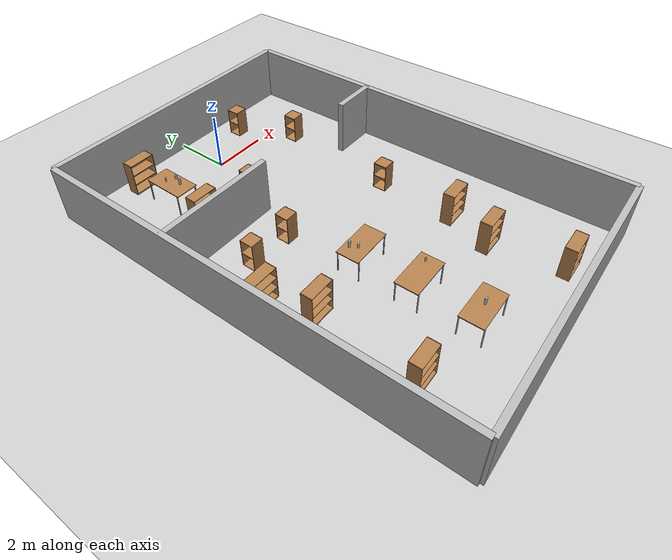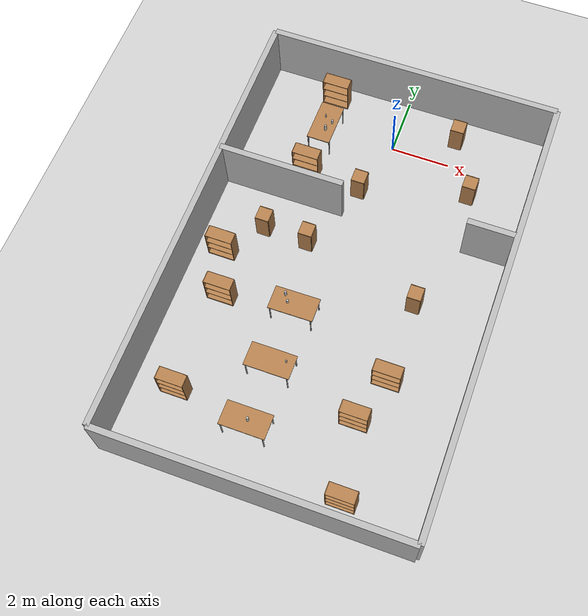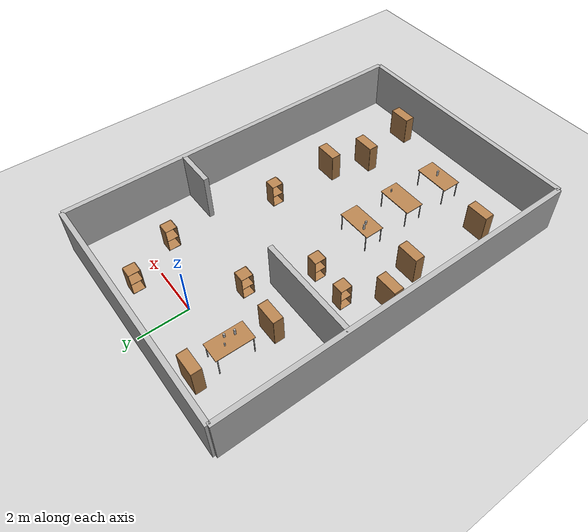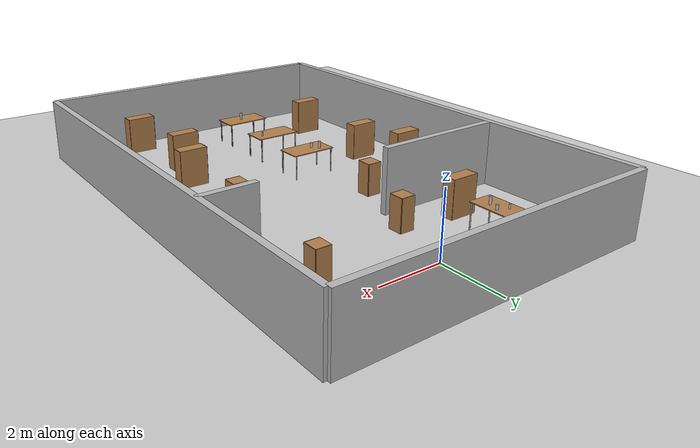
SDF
<sdf version="1.7">
 <world name="default">
  <physics type="ode">
   <ode>
    <solver>
     <type>quick</type>
     <iters>20</iters>
     <sor>1</sor>
     <use_dynamic_moi_rescaling>0</use_dynamic_moi_rescaling>
    </solver>
    <constraints>
     <cfm>0</cfm>
     <erp>0.2</erp>
     <contact_max_correcting_vel>100</contact_max_correcting_vel>
     <contact_surface_layer>0</contact_surface_layer>
    </constraints>
   </ode>
   <real_time_update_rate>1000</real_time_update_rate>
   <max_step_size>0.001</max_step_size>
   <real_time_factor>1</real_time_factor>
   <max_contacts>20</max_contacts>
  </physics>
  <light name="sun" type="directional">
   <pose>0 0 10 0 -0 0</pose>
   <diffuse>0.8 0.8 0.8 1</diffuse>
   <specular>0.2 0.2 0.2 1</specular>
   <attenuation>
    <range>1000</range>
    <constant>0.9</constant>
    <linear>0.01</linear>
    <quadratic>0.001</quadratic>
   </attenuation>
   <direction>0.5 0.1 -0.9</direction>
   <spot><inner_angle>0</inner_angle><outer_angle>0</outer_angle><falloff>0</falloff></spot>
  </light>
  <model name="ground_plane">
   <static>1</static>
   <link name="link">
    <collision name="collision">
     <geometry><plane><normal>0 0 1</normal><size>100 100</size></plane></geometry>
     <surface><friction><ode><mu>100</mu><mu2>50</mu2></ode></friction></surface>
    </collision>
    <visual name="visual">
     <cast_shadows>0</cast_shadows>
     <geometry><plane><normal>0 0 1</normal><size>100 100</size></plane></geometry>
     <material>
      <script><uri>file://media/materials/scripts/gazebo.material</uri><name>Gazebo/Grey</name></script>
     </material>
    </visual>
    <velocity_decay><linear>0</linear><angular>0</angular></velocity_decay>
   </link>
  </model>
  <model name="wall_1_model">
   <pose>0 -13 1 0 -0 0</pose>
   <static>1</static>
   <link name="wall_1_body">
    <inertial>
     <mass>1</mass>
     <inertia><ixx>1</ixx><ixy>0</ixy><ixz>0</ixz><iyy>1</iyy><iyz>0</iyz><izz>1</izz></inertia>
    </inertial>
    <collision name="collision"><geometry><box><size>10 0.2 2</size></box></geometry></collision>
    <visual name="visual"><geometry><box><size>10 0.2 2</size></box></geometry></visual>
    <velocity_decay><linear>0</linear><angular>0</angular></velocity_decay>
   </link>
  </model>
  <model name="wall_2_model">
   <pose>0 2 1 0 -0 0</pose>
   <static>1</static>
   <link name="wall_2_body">
    <inertial>
     <mass>1</mass>
     <inertia><ixx>1</ixx><ixy>0</ixy><ixz>0</ixz><iyy>1</iyy><iyz>0</iyz><izz>1</izz></inertia>
    </inertial>
    <collision name="collision"><geometry><box><size>10 0.2 2</size></box></geometry></collision>
    <visual name="visual"><geometry><box><size>10 0.2 2</size></box></geometry></visual>
    <velocity_decay><linear>0</linear><angular>0</angular></velocity_decay>
   </link>
  </model>
  <model name="wall_3_model">
   <pose>-5 -5.5 1 0 -0 0</pose>
   <static>1</static>
   <link name="wall_3_body">
    <inertial>
     <mass>1</mass>
     <inertia><ixx>1</ixx><ixy>0</ixy><ixz>0</ixz><iyy>1</iyy><iyz>0</iyz><izz>1</izz></inertia>
    </inertial>
    <collision name="collision"><geometry><box><size>0.2 15 2</size></box></geometry></collision>
    <visual name="visual"><geometry><box><size>0.2 15 2</size></box></geometry></visual>
    <velocity_decay><linear>0</linear><angular>0</angular></velocity_decay>
   </link>
  </model>
  <model name="wall_4_model">
   <pose>5 -5.5 1 0 -0 0</pose>
   <static>1</static>
   <link name="wall_4_body">
    <inertial>
     <mass>1</mass>
     <inertia><ixx>1</ixx><ixy>0</ixy><ixz>0</ixz><iyy>1</iyy><iyz>0</iyz><izz>1</izz></inertia>
    </inertial>
    <collision name="collision"><geometry><box><size>0.2 15 2</size></box></geometry></collision>
    <visual name="visual"><geometry><box><size>0.2 15 2</size></box></geometry></visual>
    <velocity_decay><linear>0</linear><angular>0</angular></velocity_decay>
   </link>
  </model>
  <model name="wall_5_model">
   <pose>-2.89886 -3 1 0 -0 0</pose>
   <static>1</static>
   <link name="wall_5_body">
    <inertial>
     <mass>1</mass>
     <inertia><ixx>1</ixx><ixy>0</ixy><ixz>0</ixz><iyy>1</iyy><iyz>0</iyz><izz>1</izz></inertia>
    </inertial>
    <collision name="collision"><geometry><box><size>4.24454 0.2 2</size></box></geometry></collision>
    <visual name="visual"><geometry><box><size>4.24454 0.2 2</size></box></geometry></visual>
    <velocity_decay><linear>0</linear><angular>0</angular></velocity_decay>
   </link>
  </model>
  <model name="wall_6_model">
   <pose>4.18871 -2.96928 1 0 -0 0</pose>
   <static>1</static>
   <link name="wall_6_body">
    <inertial>
     <mass>1</mass>
     <inertia><ixx>1</ixx><ixy>0</ixy><ixz>0</ixz><iyy>1</iyy><iyz>0</iyz><izz>1</izz></inertia>
    </inertial>
    <collision name="collision"><geometry><box><size>1.67243 0.2 2</size></box></geometry></collision>
    <visual name="visual"><geometry><box><size>1.67243 0.2 2</size></box></geometry></visual>
    <velocity_decay><linear>0</linear><angular>0</angular></velocity_decay>
   </link>
  </model>
  <scene><ambient>0.2 0.2 0.2 1</ambient><background>0.7 0.7 0.7 1</background><shadows>1</shadows></scene>
  <model name="cabinet">
   <static>0</static>
   <link name="cabinet_bottom_plate">
    <inertial>
     <pose>0 0 -1 0 -0 0</pose>
     <inertia><ixx>2.05</ixx><ixy>0</ixy><ixz>0</ixz><iyy>2.05</iyy><iyz>0</iyz><izz>2.05</izz></inertia>
     <mass>25</mass>
    </inertial>
    <collision name="cabinet_bottom_plate_geom">
     <pose>0 0 0.01 0 -0 0</pose>
     <geometry><box><size>0.45 0.45 0.02</size></box></geometry>
    </collision>
    <visual name="cabinet_bottom_plate_geom_visual">
     <pose>0 0 0.01 0 -0 0</pose>
     <geometry><box><size>0.45 0.45 0.02</size></box></geometry>
     <material>
      <script><uri>file://media/materials/scripts/gazebo.material</uri><name>Gazebo/Wood</name></script>
     </material>
    </visual>
    <collision name="cabinet_bottom_plate_geom_cabinet_back_plate">
     <pose>0.235 0 0.51 0 -0 0</pose>
     <geometry><box><size>0.02 0.45 1.02</size></box></geometry>
    </collision>
    <visual name="cabinet_bottom_plate_geom_cabinet_back_plate_visual">
     <pose>0.235 0 0.51 0 -0 0</pose>
     <geometry><box><size>0.02 0.45 1.02</size></box></geometry>
     <material>
      <script><uri>file://media/materials/scripts/gazebo.material</uri><name>Gazebo/Wood</name></script>
     </material>
    </visual>
    <collision name="cabinet_bottom_plate_geom_cabinet_left_plate">
     <pose>0 0.235 0.51 0 -0 0</pose>
     <geometry><box><size>0.45 0.02 1.02</size></box></geometry>
    </collision>
    <visual name="cabinet_bottom_plate_geom_cabinet_left_plate_visual">
     <pose>0 0.235 0.51 0 -0 0</pose>
     <geometry><box><size>0.45 0.02 1.02</size></box></geometry>
     <material>
      <script><uri>file://media/materials/scripts/gazebo.material</uri><name>Gazebo/Wood</name></script>
     </material>
    </visual>
    <collision name="cabinet_bottom_plate_geom_cabinet_middle_plate">
     <pose>0 0 0.51 0 -0 0</pose>
     <geometry><box><size>0.45 0.45 0.02</size></box></geometry>
    </collision>
    <visual name="cabinet_bottom_plate_geom_cabinet_middle_plate_visual">
     <pose>0 0 0.51 0 -0 0</pose>
     <geometry><box><size>0.45 0.45 0.02</size></box></geometry>
     <material>
      <script><uri>file://media/materials/scripts/gazebo.material</uri><name>Gazebo/Wood</name></script>
     </material>
    </visual>
    <collision name="cabinet_bottom_plate_geom_cabinet_right_plate">
     <pose>0 -0.235 0.51 0 -0 0</pose>
     <geometry><box><size>0.45 0.02 1.02</size></box></geometry>
    </collision>
    <visual name="cabinet_bottom_plate_geom_cabinet_right_plate_visual">
     <pose>0 -0.235 0.51 0 -0 0</pose>
     <geometry><box><size>0.45 0.02 1.02</size></box></geometry>
     <material>
      <script><uri>file://media/materials/scripts/gazebo.material</uri><name>Gazebo/Wood</name></script>
     </material>
    </visual>
    <collision name="cabinet_bottom_plate_geom_cabinet_top_plate">
     <pose>0 0 1.01 0 -0 0</pose>
     <geometry><box><size>0.45 0.45 0.02</size></box></geometry>
    </collision>
    <visual name="cabinet_bottom_plate_geom_cabinet_top_plate_visual">
     <pose>0 0 1.01 0 -0 0</pose>
     <geometry><box><size>0.45 0.45 0.02</size></box></geometry>
     <material>
      <script><uri>file://media/materials/scripts/gazebo.material</uri><name>Gazebo/Wood</name></script>
     </material>
    </visual>
    <velocity_decay><linear>0</linear><angular>0</angular></velocity_decay>
   </link>
   <pose>1.99517 1.00009 0 0 -1e-06 -0.000426</pose>
  </model>
  <model name="cabinet_0">
   <static>0</static>
   <link name="cabinet_bottom_plate">
    <inertial>
     <pose>0 0 -1 0 -0 0</pose>
     <inertia><ixx>2.05</ixx><ixy>0</ixy><ixz>0</ixz><iyy>2.05</iyy><iyz>0</iyz><izz>2.05</izz></inertia>
     <mass>25</mass>
    </inertial>
    <collision name="cabinet_bottom_plate_geom">
     <pose>0 0 0.01 0 -0 0</pose>
     <geometry><box><size>0.45 0.45 0.02</size></box></geometry>
    </collision>
    <visual name="cabinet_bottom_plate_geom_visual">
     <pose>0 0 0.01 0 -0 0</pose>
     <geometry><box><size>0.45 0.45 0.02</size></box></geometry>
     <material>
      <script><uri>file://media/materials/scripts/gazebo.material</uri><name>Gazebo/Wood</name></script>
     </material>
    </visual>
    <collision name="cabinet_bottom_plate_geom_cabinet_back_plate">
     <pose>0.235 0 0.51 0 -0 0</pose>
     <geometry><box><size>0.02 0.45 1.02</size></box></geometry>
    </collision>
    <visual name="cabinet_bottom_plate_geom_cabinet_back_plate_visual">
     <pose>0.235 0 0.51 0 -0 0</pose>
     <geometry><box><size>0.02 0.45 1.02</size></box></geometry>
     <material>
      <script><uri>file://media/materials/scripts/gazebo.material</uri><name>Gazebo/Wood</name></script>
     </material>
    </visual>
    <collision name="cabinet_bottom_plate_geom_cabinet_left_plate">
     <pose>0 0.235 0.51 0 -0 0</pose>
     <geometry><box><size>0.45 0.02 1.02</size></box></geometry>
    </collision>
    <visual name="cabinet_bottom_plate_geom_cabinet_left_plate_visual">
     <pose>0 0.235 0.51 0 -0 0</pose>
     <geometry><box><size>0.45 0.02 1.02</size></box></geometry>
     <material>
      <script><uri>file://media/materials/scripts/gazebo.material</uri><name>Gazebo/Wood</name></script>
     </material>
    </visual>
    <collision name="cabinet_bottom_plate_geom_cabinet_middle_plate">
     <pose>0 0 0.51 0 -0 0</pose>
     <geometry><box><size>0.45 0.45 0.02</size></box></geometry>
    </collision>
    <visual name="cabinet_bottom_plate_geom_cabinet_middle_plate_visual">
     <pose>0 0 0.51 0 -0 0</pose>
     <geometry><box><size>0.45 0.45 0.02</size></box></geometry>
     <material>
      <script><uri>file://media/materials/scripts/gazebo.material</uri><name>Gazebo/Wood</name></script>
     </material>
    </visual>
    <collision name="cabinet_bottom_plate_geom_cabinet_right_plate">
     <pose>0 -0.235 0.51 0 -0 0</pose>
     <geometry><box><size>0.45 0.02 1.02</size></box></geometry>
    </collision>
    <visual name="cabinet_bottom_plate_geom_cabinet_right_plate_visual">
     <pose>0 -0.235 0.51 0 -0 0</pose>
     <geometry><box><size>0.45 0.02 1.02</size></box></geometry>
     <material>
      <script><uri>file://media/materials/scripts/gazebo.material</uri><name>Gazebo/Wood</name></script>
     </material>
    </visual>
    <collision name="cabinet_bottom_plate_geom_cabinet_top_plate">
     <pose>0 0 1.01 0 -0 0</pose>
     <geometry><box><size>0.45 0.45 0.02</size></box></geometry>
    </collision>
    <visual name="cabinet_bottom_plate_geom_cabinet_top_plate_visual">
     <pose>0 0 1.01 0 -0 0</pose>
     <geometry><box><size>0.45 0.45 0.02</size></box></geometry>
     <material>
      <script><uri>file://media/materials/scripts/gazebo.material</uri><name>Gazebo/Wood</name></script>
     </material>
    </visual>
    <velocity_decay><linear>0</linear><angular>0</angular></velocity_decay>
   </link>
   <pose>2.51075 -5.43934 0 0 -1e-06 -0.003769</pose>
  </model>
  <model name="bookshelf">
   <static>0</static>
   <link name="link">
    <inertial>
     <mass>1</mass>
     <inertia><ixx>1</ixx><ixy>0</ixy><ixz>0</ixz><iyy>1</iyy><iyz>0</iyz><izz>1</izz></inertia>
    </inertial>
    <collision name="back">
     <pose>0 0.005 0.6 0 -0 0</pose>
     <geometry><box><size>0.9 0.01 1.2</size></box></geometry>
    </collision>
    <visual name="visual1">
     <pose>0 0.005 0.6 0 -0 0</pose>
     <geometry><box><size>0.9 0.01 1.2</size></box></geometry>
     <material>
      <script><uri>file://media/materials/scripts/gazebo.material</uri><name>Gazebo/Wood</name></script>
     </material>
    </visual>
    <collision name="left_side">
     <pose>0.45 -0.195 0.6 0 -0 0</pose>
     <geometry><box><size>0.02 0.4 1.2</size></box></geometry>
    </collision>
    <visual name="visual2">
     <pose>0.45 -0.195 0.6 0 -0 0</pose>
     <geometry><box><size>0.02 0.4 1.2</size></box></geometry>
     <material>
      <script><uri>file://media/materials/scripts/gazebo.material</uri><name>Gazebo/Wood</name></script>
     </material>
    </visual>
    <collision name="right_side">
     <pose>-0.45 -0.195 0.6 0 -0 0</pose>
     <geometry><box><size>0.02 0.4 1.2</size></box></geometry>
    </collision>
    <visual name="visual3">
     <pose>-0.45 -0.195 0.6 0 -0 0</pose>
     <geometry><box><size>0.02 0.4 1.2</size></box></geometry>
     <material>
      <script><uri>file://media/materials/scripts/gazebo.material</uri><name>Gazebo/Wood</name></script>
     </material>
    </visual>
    <collision name="bottom">
     <pose>0 -0.195 0.03 0 -0 0</pose>
     <geometry><box><size>0.88 0.4 0.06</size></box></geometry>
    </collision>
    <visual name="visual4">
     <pose>0 -0.195 0.03 0 -0 0</pose>
     <geometry><box><size>0.88 0.4 0.06</size></box></geometry>
     <material>
      <script><uri>file://media/materials/scripts/gazebo.material</uri><name>Gazebo/Wood</name></script>
     </material>
    </visual>
    <collision name="top">
     <pose>0 -0.195 1.19 0 -0 0</pose>
     <geometry><box><size>0.88 0.4 0.02</size></box></geometry>
    </collision>
    <visual name="visual5">
     <pose>0 -0.195 1.19 0 -0 0</pose>
     <geometry><box><size>0.88 0.4 0.02</size></box></geometry>
     <material>
      <script><uri>file://media/materials/scripts/gazebo.material</uri><name>Gazebo/Wood</name></script>
     </material>
    </visual>
    <collision name="low_shelf">
     <pose>0 -0.195 0.43 0 -0 0</pose>
     <geometry><box><size>0.88 0.4 0.02</size></box></geometry>
    </collision>
    <visual name="visual6">
     <pose>0 -0.195 0.43 0 -0 0</pose>
     <geometry><box><size>0.88 0.4 0.02</size></box></geometry>
     <material>
      <script><uri>file://media/materials/scripts/gazebo.material</uri><name>Gazebo/Wood</name></script>
     </material>
    </visual>
    <collision name="high_shelf">
     <pose>0 -0.195 0.8 0 -0 0</pose>
     <geometry><box><size>0.88 0.4 0.02</size></box></geometry>
    </collision>
    <visual name="visual7">
     <pose>0 -0.195 0.8 0 -0 0</pose>
     <geometry><box><size>0.88 0.4 0.02</size></box></geometry>
     <material>
      <script><uri>file://media/materials/scripts/gazebo.material</uri><name>Gazebo/Wood</name></script>
     </material>
    </visual>
    <velocity_decay><linear>0</linear><angular>0</angular></velocity_decay>
   </link>
   <pose>2 -9.55401 0 -5e-06 0 0</pose>
  </model>
  <model name="bookshelf_0">
   <static>0</static>
   <link name="link">
    <inertial>
     <mass>1</mass>
     <inertia><ixx>1</ixx><ixy>0</ixy><ixz>0</ixz><iyy>1</iyy><iyz>0</iyz><izz>1</izz></inertia>
    </inertial>
    <collision name="back">
     <pose>0 0.005 0.6 0 -0 0</pose>
     <geometry><box><size>0.9 0.01 1.2</size></box></geometry>
    </collision>
    <visual name="visual1">
     <pose>0 0.005 0.6 0 -0 0</pose>
     <geometry><box><size>0.9 0.01 1.2</size></box></geometry>
     <material>
      <script><uri>file://media/materials/scripts/gazebo.material</uri><name>Gazebo/Wood</name></script>
     </material>
    </visual>
    <collision name="left_side">
     <pose>0.45 -0.195 0.6 0 -0 0</pose>
     <geometry><box><size>0.02 0.4 1.2</size></box></geometry>
    </collision>
    <visual name="visual2">
     <pose>0.45 -0.195 0.6 0 -0 0</pose>
     <geometry><box><size>0.02 0.4 1.2</size></box></geometry>
     <material>
      <script><uri>file://media/materials/scripts/gazebo.material</uri><name>Gazebo/Wood</name></script>
     </material>
    </visual>
    <collision name="right_side">
     <pose>-0.45 -0.195 0.6 0 -0 0</pose>
     <geometry><box><size>0.02 0.4 1.2</size></box></geometry>
    </collision>
    <visual name="visual3">
     <pose>-0.45 -0.195 0.6 0 -0 0</pose>
     <geometry><box><size>0.02 0.4 1.2</size></box></geometry>
     <material>
      <script><uri>file://media/materials/scripts/gazebo.material</uri><name>Gazebo/Wood</name></script>
     </material>
    </visual>
    <collision name="bottom">
     <pose>0 -0.195 0.03 0 -0 0</pose>
     <geometry><box><size>0.88 0.4 0.06</size></box></geometry>
    </collision>
    <visual name="visual4">
     <pose>0 -0.195 0.03 0 -0 0</pose>
     <geometry><box><size>0.88 0.4 0.06</size></box></geometry>
     <material>
      <script><uri>file://media/materials/scripts/gazebo.material</uri><name>Gazebo/Wood</name></script>
     </material>
    </visual>
    <collision name="top">
     <pose>0 -0.195 1.19 0 -0 0</pose>
     <geometry><box><size>0.88 0.4 0.02</size></box></geometry>
    </collision>
    <visual name="visual5">
     <pose>0 -0.195 1.19 0 -0 0</pose>
     <geometry><box><size>0.88 0.4 0.02</size></box></geometry>
     <material>
      <script><uri>file://media/materials/scripts/gazebo.material</uri><name>Gazebo/Wood</name></script>
     </material>
    </visual>
    <collision name="low_shelf">
     <pose>0 -0.195 0.43 0 -0 0</pose>
     <geometry><box><size>0.88 0.4 0.02</size></box></geometry>
    </collision>
    <visual name="visual6">
     <pose>0 -0.195 0.43 0 -0 0</pose>
     <geometry><box><size>0.88 0.4 0.02</size></box></geometry>
     <material>
      <script><uri>file://media/materials/scripts/gazebo.material</uri><name>Gazebo/Wood</name></script>
     </material>
    </visual>
    <collision name="high_shelf">
     <pose>0 -0.195 0.8 0 -0 0</pose>
     <geometry><box><size>0.88 0.4 0.02</size></box></geometry>
    </collision>
    <visual name="visual7">
     <pose>0 -0.195 0.8 0 -0 0</pose>
     <geometry><box><size>0.88 0.4 0.02</size></box></geometry>
     <material>
      <script><uri>file://media/materials/scripts/gazebo.material</uri><name>Gazebo/Wood</name></script>
     </material>
    </visual>
    <velocity_decay><linear>0</linear><angular>0</angular></velocity_decay>
   </link>
   <pose>-2.49657 -1.57894 0 -1.7e-05 0 0</pose>
  </model>
  <model name="bookshelf_1">
   <static>0</static>
   <link name="link">
    <inertial>
     <mass>1</mass>
     <inertia><ixx>1</ixx><ixy>0</ixy><ixz>0</ixz><iyy>1</iyy><iyz>0</iyz><izz>1</izz></inertia>
    </inertial>
    <collision name="back">
     <pose>0 0.005 0.6 0 -0 0</pose>
     <geometry><box><size>0.9 0.01 1.2</size></box></geometry>
    </collision>
    <visual name="visual1">
     <pose>0 0.005 0.6 0 -0 0</pose>
     <geometry><box><size>0.9 0.01 1.2</size></box></geometry>
     <material>
      <script><uri>file://media/materials/scripts/gazebo.material</uri><name>Gazebo/Wood</name></script>
     </material>
    </visual>
    <collision name="left_side">
     <pose>0.45 -0.195 0.6 0 -0 0</pose>
     <geometry><box><size>0.02 0.4 1.2</size></box></geometry>
    </collision>
    <visual name="visual2">
     <pose>0.45 -0.195 0.6 0 -0 0</pose>
     <geometry><box><size>0.02 0.4 1.2</size></box></geometry>
     <material>
      <script><uri>file://media/materials/scripts/gazebo.material</uri><name>Gazebo/Wood</name></script>
     </material>
    </visual>
    <collision name="right_side">
     <pose>-0.45 -0.195 0.6 0 -0 0</pose>
     <geometry><box><size>0.02 0.4 1.2</size></box></geometry>
    </collision>
    <visual name="visual3">
     <pose>-0.45 -0.195 0.6 0 -0 0</pose>
     <geometry><box><size>0.02 0.4 1.2</size></box></geometry>
     <material>
      <script><uri>file://media/materials/scripts/gazebo.material</uri><name>Gazebo/Wood</name></script>
     </material>
    </visual>
    <collision name="bottom">
     <pose>0 -0.195 0.03 0 -0 0</pose>
     <geometry><box><size>0.88 0.4 0.06</size></box></geometry>
    </collision>
    <visual name="visual4">
     <pose>0 -0.195 0.03 0 -0 0</pose>
     <geometry><box><size>0.88 0.4 0.06</size></box></geometry>
     <material>
      <script><uri>file://media/materials/scripts/gazebo.material</uri><name>Gazebo/Wood</name></script>
     </material>
    </visual>
    <collision name="top">
     <pose>0 -0.195 1.19 0 -0 0</pose>
     <geometry><box><size>0.88 0.4 0.02</size></box></geometry>
    </collision>
    <visual name="visual5">
     <pose>0 -0.195 1.19 0 -0 0</pose>
     <geometry><box><size>0.88 0.4 0.02</size></box></geometry>
     <material>
      <script><uri>file://media/materials/scripts/gazebo.material</uri><name>Gazebo/Wood</name></script>
     </material>
    </visual>
    <collision name="low_shelf">
     <pose>0 -0.195 0.43 0 -0 0</pose>
     <geometry><box><size>0.88 0.4 0.02</size></box></geometry>
    </collision>
    <visual name="visual6">
     <pose>0 -0.195 0.43 0 -0 0</pose>
     <geometry><box><size>0.88 0.4 0.02</size></box></geometry>
     <material>
      <script><uri>file://media/materials/scripts/gazebo.material</uri><name>Gazebo/Wood</name></script>
     </material>
    </visual>
    <collision name="high_shelf">
     <pose>0 -0.195 0.8 0 -0 0</pose>
     <geometry><box><size>0.88 0.4 0.02</size></box></geometry>
    </collision>
    <visual name="visual7">
     <pose>0 -0.195 0.8 0 -0 0</pose>
     <geometry><box><size>0.88 0.4 0.02</size></box></geometry>
     <material>
      <script><uri>file://media/materials/scripts/gazebo.material</uri><name>Gazebo/Wood</name></script>
     </material>
    </visual>
    <velocity_decay><linear>0</linear><angular>0</angular></velocity_decay>
   </link>
   <pose>-2.49816 1.46785 -1e-06 -2.2e-05 2e-06 -3e-06</pose>
  </model>
  <model name="table">
   <static>0</static>
   <link name="link">
    <collision name="surface">
     <pose>0 0 0.9 0 -0 0</pose>
     <geometry><box><size>1.5 0.8 0.03</size></box></geometry>
    </collision>
    <visual name="visual1">
     <pose>0 0 0.9 0 -0 0</pose>
     <geometry><box><size>1.5 0.8 0.03</size></box></geometry>
     <material>
      <script><uri>file://media/materials/scripts/gazebo.material</uri><name>Gazebo/Wood</name></script>
     </material>
    </visual>
    <collision name="front_left_leg">
     <pose>0.68 0.38 0.5 0 -0 0</pose>
     <geometry><cylinder><radius>0.02</radius><length>0.8</length></cylinder></geometry>
    </collision>
    <visual name="front_left_leg">
     <pose>0.68 0.38 0.5 0 -0 0</pose>
     <geometry><cylinder><radius>0.02</radius><length>0.8</length></cylinder></geometry>
     <material>
      <script><uri>file://media/materials/scripts/gazebo.material</uri><name>Gazebo/Grey</name></script>
     </material>
    </visual>
    <collision name="front_right_leg">
     <pose>0.68 -0.38 0.5 0 -0 0</pose>
     <geometry><cylinder><radius>0.02</radius><length>0.8</length></cylinder></geometry>
    </collision>
    <visual name="front_right_leg">
     <pose>0.68 -0.38 0.5 0 -0 0</pose>
     <geometry><cylinder><radius>0.02</radius><length>0.8</length></cylinder></geometry>
     <material>
      <script><uri>file://media/materials/scripts/gazebo.material</uri><name>Gazebo/Grey</name></script>
     </material>
    </visual>
    <collision name="back_right_leg">
     <pose>-0.68 -0.38 0.5 0 -0 0</pose>
     <geometry><cylinder><radius>0.02</radius><length>0.8</length></cylinder></geometry>
    </collision>
    <visual name="back_right_leg">
     <pose>-0.68 -0.38 0.5 0 -0 0</pose>
     <geometry><cylinder><radius>0.02</radius><length>0.8</length></cylinder></geometry>
     <material>
      <script><uri>file://media/materials/scripts/gazebo.material</uri><name>Gazebo/Grey</name></script>
     </material>
    </visual>
    <collision name="back_left_leg">
     <pose>-0.68 0.38 0.5 0 -0 0</pose>
     <geometry><cylinder><radius>0.02</radius><length>0.8</length></cylinder></geometry>
    </collision>
    <visual name="back_left_leg">
     <pose>-0.68 0.38 0.5 0 -0 0</pose>
     <geometry><cylinder><radius>0.02</radius><length>0.8</length></cylinder></geometry>
     <material>
      <script><uri>file://media/materials/scripts/gazebo.material</uri><name>Gazebo/Grey</name></script>
     </material>
    </visual>
    <velocity_decay><linear>0</linear><angular>0</angular></velocity_decay>
    <inertial>
     <inertia><ixx>1</ixx><ixy>0</ixy><ixz>0</ixz><iyy>1</iyy><iyz>0</iyz><izz>1</izz></inertia>
     <mass>1</mass>
    </inertial>
   </link>
   <pose>-1.00064 -8.99574 -0.105007 -8e-06 5.2e-05 -0.000544</pose>
  </model>
  <model name="cabinet_1">
   <static>0</static>
   <link name="cabinet_bottom_plate">
    <inertial>
     <pose>0 0 -1 0 -0 0</pose>
     <inertia><ixx>2.05</ixx><ixy>0</ixy><ixz>0</ixz><iyy>2.05</iyy><iyz>0</iyz><izz>2.05</izz></inertia>
     <mass>25</mass>
    </inertial>
    <collision name="cabinet_bottom_plate_geom">
     <pose>0 0 0.01 0 -0 0</pose>
     <geometry><box><size>0.45 0.45 0.02</size></box></geometry>
    </collision>
    <visual name="cabinet_bottom_plate_geom_visual">
     <pose>0 0 0.01 0 -0 0</pose>
     <geometry><box><size>0.45 0.45 0.02</size></box></geometry>
     <material>
      <script><uri>file://media/materials/scripts/gazebo.material</uri><name>Gazebo/Wood</name></script>
     </material>
    </visual>
    <collision name="cabinet_bottom_plate_geom_cabinet_back_plate">
     <pose>0.235 0 0.51 0 -0 0</pose>
     <geometry><box><size>0.02 0.45 1.02</size></box></geometry>
    </collision>
    <visual name="cabinet_bottom_plate_geom_cabinet_back_plate_visual">
     <pose>0.235 0 0.51 0 -0 0</pose>
     <geometry><box><size>0.02 0.45 1.02</size></box></geometry>
     <material>
      <script><uri>file://media/materials/scripts/gazebo.material</uri><name>Gazebo/Wood</name></script>
     </material>
    </visual>
    <collision name="cabinet_bottom_plate_geom_cabinet_left_plate">
     <pose>0 0.235 0.51 0 -0 0</pose>
     <geometry><box><size>0.45 0.02 1.02</size></box></geometry>
    </collision>
    <visual name="cabinet_bottom_plate_geom_cabinet_left_plate_visual">
     <pose>0 0.235 0.51 0 -0 0</pose>
     <geometry><box><size>0.45 0.02 1.02</size></box></geometry>
     <material>
      <script><uri>file://media/materials/scripts/gazebo.material</uri><name>Gazebo/Wood</name></script>
     </material>
    </visual>
    <collision name="cabinet_bottom_plate_geom_cabinet_middle_plate">
     <pose>0 0 0.51 0 -0 0</pose>
     <geometry><box><size>0.45 0.45 0.02</size></box></geometry>
    </collision>
    <visual name="cabinet_bottom_plate_geom_cabinet_middle_plate_visual">
     <pose>0 0 0.51 0 -0 0</pose>
     <geometry><box><size>0.45 0.45 0.02</size></box></geometry>
     <material>
      <script><uri>file://media/materials/scripts/gazebo.material</uri><name>Gazebo/Wood</name></script>
     </material>
    </visual>
    <collision name="cabinet_bottom_plate_geom_cabinet_right_plate">
     <pose>0 -0.235 0.51 0 -0 0</pose>
     <geometry><box><size>0.45 0.02 1.02</size></box></geometry>
    </collision>
    <visual name="cabinet_bottom_plate_geom_cabinet_right_plate_visual">
     <pose>0 -0.235 0.51 0 -0 0</pose>
     <geometry><box><size>0.45 0.02 1.02</size></box></geometry>
     <material>
      <script><uri>file://media/materials/scripts/gazebo.material</uri><name>Gazebo/Wood</name></script>
     </material>
    </visual>
    <collision name="cabinet_bottom_plate_geom_cabinet_top_plate">
     <pose>0 0 1.01 0 -0 0</pose>
     <geometry><box><size>0.45 0.45 0.02</size></box></geometry>
    </collision>
    <visual name="cabinet_bottom_plate_geom_cabinet_top_plate_visual">
     <pose>0 0 1.01 0 -0 0</pose>
     <geometry><box><size>0.45 0.45 0.02</size></box></geometry>
     <material>
      <script><uri>file://media/materials/scripts/gazebo.material</uri><name>Gazebo/Wood</name></script>
     </material>
    </visual>
    <velocity_decay><linear>0</linear><angular>0</angular></velocity_decay>
   </link>
   <pose>-3.00498 -4.39991 0 0 -1e-06 -0.003769</pose>
  </model>
  <model name="cabinet_2">
   <static>0</static>
   <link name="cabinet_bottom_plate">
    <inertial>
     <pose>0 0 -1 0 -0 0</pose>
     <inertia><ixx>2.05</ixx><ixy>0</ixy><ixz>0</ixz><iyy>2.05</iyy><iyz>0</iyz><izz>2.05</izz></inertia>
     <mass>25</mass>
    </inertial>
    <collision name="cabinet_bottom_plate_geom">
     <pose>0 0 0.01 0 -0 0</pose>
     <geometry><box><size>0.45 0.45 0.02</size></box></geometry>
    </collision>
    <visual name="cabinet_bottom_plate_geom_visual">
     <pose>0 0 0.01 0 -0 0</pose>
     <geometry><box><size>0.45 0.45 0.02</size></box></geometry>
     <material>
      <script><uri>file://media/materials/scripts/gazebo.material</uri><name>Gazebo/Wood</name></script>
     </material>
    </visual>
    <collision name="cabinet_bottom_plate_geom_cabinet_back_plate">
     <pose>0.235 0 0.51 0 -0 0</pose>
     <geometry><box><size>0.02 0.45 1.02</size></box></geometry>
    </collision>
    <visual name="cabinet_bottom_plate_geom_cabinet_back_plate_visual">
     <pose>0.235 0 0.51 0 -0 0</pose>
     <geometry><box><size>0.02 0.45 1.02</size></box></geometry>
     <material>
      <script><uri>file://media/materials/scripts/gazebo.material</uri><name>Gazebo/Wood</name></script>
     </material>
    </visual>
    <collision name="cabinet_bottom_plate_geom_cabinet_left_plate">
     <pose>0 0.235 0.51 0 -0 0</pose>
     <geometry><box><size>0.45 0.02 1.02</size></box></geometry>
    </collision>
    <visual name="cabinet_bottom_plate_geom_cabinet_left_plate_visual">
     <pose>0 0.235 0.51 0 -0 0</pose>
     <geometry><box><size>0.45 0.02 1.02</size></box></geometry>
     <material>
      <script><uri>file://media/materials/scripts/gazebo.material</uri><name>Gazebo/Wood</name></script>
     </material>
    </visual>
    <collision name="cabinet_bottom_plate_geom_cabinet_middle_plate">
     <pose>0 0 0.51 0 -0 0</pose>
     <geometry><box><size>0.45 0.45 0.02</size></box></geometry>
    </collision>
    <visual name="cabinet_bottom_plate_geom_cabinet_middle_plate_visual">
     <pose>0 0 0.51 0 -0 0</pose>
     <geometry><box><size>0.45 0.45 0.02</size></box></geometry>
     <material>
      <script><uri>file://media/materials/scripts/gazebo.material</uri><name>Gazebo/Wood</name></script>
     </material>
    </visual>
    <collision name="cabinet_bottom_plate_geom_cabinet_right_plate">
     <pose>0 -0.235 0.51 0 -0 0</pose>
     <geometry><box><size>0.45 0.02 1.02</size></box></geometry>
    </collision>
    <visual name="cabinet_bottom_plate_geom_cabinet_right_plate_visual">
     <pose>0 -0.235 0.51 0 -0 0</pose>
     <geometry><box><size>0.45 0.02 1.02</size></box></geometry>
     <material>
      <script><uri>file://media/materials/scripts/gazebo.material</uri><name>Gazebo/Wood</name></script>
     </material>
    </visual>
    <collision name="cabinet_bottom_plate_geom_cabinet_top_plate">
     <pose>0 0 1.01 0 -0 0</pose>
     <geometry><box><size>0.45 0.45 0.02</size></box></geometry>
    </collision>
    <visual name="cabinet_bottom_plate_geom_cabinet_top_plate_visual">
     <pose>0 0 1.01 0 -0 0</pose>
     <geometry><box><size>0.45 0.45 0.02</size></box></geometry>
     <material>
      <script><uri>file://media/materials/scripts/gazebo.material</uri><name>Gazebo/Wood</name></script>
     </material>
    </visual>
    <velocity_decay><linear>0</linear><angular>0</angular></velocity_decay>
   </link>
   <pose>-1.49681 -4.45607 0 0 -1e-06 -0.003769</pose>
  </model>
  <model name="bookshelf_2">
   <static>0</static>
   <link name="link">
    <inertial>
     <mass>1</mass>
     <inertia><ixx>1</ixx><ixy>0</ixy><ixz>0</ixz><iyy>1</iyy><iyz>0</iyz><izz>1</izz></inertia>
    </inertial>
    <collision name="back">
     <pose>0 0.005 0.6 0 -0 0</pose>
     <geometry><box><size>0.9 0.01 1.2</size></box></geometry>
    </collision>
    <visual name="visual1">
     <pose>0 0.005 0.6 0 -0 0</pose>
     <geometry><box><size>0.9 0.01 1.2</size></box></geometry>
     <material>
      <script><uri>file://media/materials/scripts/gazebo.material</uri><name>Gazebo/Wood</name></script>
     </material>
    </visual>
    <collision name="left_side">
     <pose>0.45 -0.195 0.6 0 -0 0</pose>
     <geometry><box><size>0.02 0.4 1.2</size></box></geometry>
    </collision>
    <visual name="visual2">
     <pose>0.45 -0.195 0.6 0 -0 0</pose>
     <geometry><box><size>0.02 0.4 1.2</size></box></geometry>
     <material>
      <script><uri>file://media/materials/scripts/gazebo.material</uri><name>Gazebo/Wood</name></script>
     </material>
    </visual>
    <collision name="right_side">
     <pose>-0.45 -0.195 0.6 0 -0 0</pose>
     <geometry><box><size>0.02 0.4 1.2</size></box></geometry>
    </collision>
    <visual name="visual3">
     <pose>-0.45 -0.195 0.6 0 -0 0</pose>
     <geometry><box><size>0.02 0.4 1.2</size></box></geometry>
     <material>
      <script><uri>file://media/materials/scripts/gazebo.material</uri><name>Gazebo/Wood</name></script>
     </material>
    </visual>
    <collision name="bottom">
     <pose>0 -0.195 0.03 0 -0 0</pose>
     <geometry><box><size>0.88 0.4 0.06</size></box></geometry>
    </collision>
    <visual name="visual4">
     <pose>0 -0.195 0.03 0 -0 0</pose>
     <geometry><box><size>0.88 0.4 0.06</size></box></geometry>
     <material>
      <script><uri>file://media/materials/scripts/gazebo.material</uri><name>Gazebo/Wood</name></script>
     </material>
    </visual>
    <collision name="top">
     <pose>0 -0.195 1.19 0 -0 0</pose>
     <geometry><box><size>0.88 0.4 0.02</size></box></geometry>
    </collision>
    <visual name="visual5">
     <pose>0 -0.195 1.19 0 -0 0</pose>
     <geometry><box><size>0.88 0.4 0.02</size></box></geometry>
     <material>
      <script><uri>file://media/materials/scripts/gazebo.material</uri><name>Gazebo/Wood</name></script>
     </material>
    </visual>
    <collision name="low_shelf">
     <pose>0 -0.195 0.43 0 -0 0</pose>
     <geometry><box><size>0.88 0.4 0.02</size></box></geometry>
    </collision>
    <visual name="visual6">
     <pose>0 -0.195 0.43 0 -0 0</pose>
     <geometry><box><size>0.88 0.4 0.02</size></box></geometry>
     <material>
      <script><uri>file://media/materials/scripts/gazebo.material</uri><name>Gazebo/Wood</name></script>
     </material>
    </visual>
    <collision name="high_shelf">
     <pose>0 -0.195 0.8 0 -0 0</pose>
     <geometry><box><size>0.88 0.4 0.02</size></box></geometry>
    </collision>
    <visual name="visual7">
     <pose>0 -0.195 0.8 0 -0 0</pose>
     <geometry><box><size>0.88 0.4 0.02</size></box></geometry>
     <material>
      <script><uri>file://media/materials/scripts/gazebo.material</uri><name>Gazebo/Wood</name></script>
     </material>
    </visual>
    <velocity_decay><linear>0</linear><angular>0</angular></velocity_decay>
   </link>
   <pose>-3.41849 -7 -1e-06 -2.3e-05 3e-06 0</pose>
  </model>
  <model name="table_0">
   <static>0</static>
   <link name="link">
    <collision name="surface">
     <pose>0 0 0.9 0 -0 0</pose>
     <geometry><box><size>1.5 0.8 0.03</size></box></geometry>
    </collision>
    <visual name="visual1">
     <pose>0 0 0.9 0 -0 0</pose>
     <geometry><box><size>1.5 0.8 0.03</size></box></geometry>
     <material>
      <script><uri>file://media/materials/scripts/gazebo.material</uri><name>Gazebo/Wood</name></script>
     </material>
    </visual>
    <collision name="front_left_leg">
     <pose>0.68 0.38 0.5 0 -0 0</pose>
     <geometry><cylinder><radius>0.02</radius><length>0.8</length></cylinder></geometry>
    </collision>
    <visual name="front_left_leg">
     <pose>0.68 0.38 0.5 0 -0 0</pose>
     <geometry><cylinder><radius>0.02</radius><length>0.8</length></cylinder></geometry>
     <material>
      <script><uri>file://media/materials/scripts/gazebo.material</uri><name>Gazebo/Grey</name></script>
     </material>
    </visual>
    <collision name="front_right_leg">
     <pose>0.68 -0.38 0.5 0 -0 0</pose>
     <geometry><cylinder><radius>0.02</radius><length>0.8</length></cylinder></geometry>
    </collision>
    <visual name="front_right_leg">
     <pose>0.68 -0.38 0.5 0 -0 0</pose>
     <geometry><cylinder><radius>0.02</radius><length>0.8</length></cylinder></geometry>
     <material>
      <script><uri>file://media/materials/scripts/gazebo.material</uri><name>Gazebo/Grey</name></script>
     </material>
    </visual>
    <collision name="back_right_leg">
     <pose>-0.68 -0.38 0.5 0 -0 0</pose>
     <geometry><cylinder><radius>0.02</radius><length>0.8</length></cylinder></geometry>
    </collision>
    <visual name="back_right_leg">
     <pose>-0.68 -0.38 0.5 0 -0 0</pose>
     <geometry><cylinder><radius>0.02</radius><length>0.8</length></cylinder></geometry>
     <material>
      <script><uri>file://media/materials/scripts/gazebo.material</uri><name>Gazebo/Grey</name></script>
     </material>
    </visual>
    <collision name="back_left_leg">
     <pose>-0.68 0.38 0.5 0 -0 0</pose>
     <geometry><cylinder><radius>0.02</radius><length>0.8</length></cylinder></geometry>
    </collision>
    <visual name="back_left_leg">
     <pose>-0.68 0.38 0.5 0 -0 0</pose>
     <geometry><cylinder><radius>0.02</radius><length>0.8</length></cylinder></geometry>
     <material>
      <script><uri>file://media/materials/scripts/gazebo.material</uri><name>Gazebo/Grey</name></script>
     </material>
    </visual>
    <velocity_decay><linear>0</linear><angular>0</angular></velocity_decay>
    <inertial>
     <inertia><ixx>1</ixx><ixy>0</ixy><ixz>0</ixz><iyy>1</iyy><iyz>0</iyz><izz>1</izz></inertia>
     <mass>1</mass>
    </inertial>
   </link>
   <pose>-0.9933 -6.97211 -0.111429 -0.00054 -0.00169 0.010892</pose>
  </model>
  <model name="table_1">
   <static>0</static>
   <link name="link">
    <collision name="surface">
     <pose>0 0 0.9 0 -0 0</pose>
     <geometry><box><size>1.5 0.8 0.03</size></box></geometry>
    </collision>
    <visual name="visual1">
     <pose>0 0 0.9 0 -0 0</pose>
     <geometry><box><size>1.5 0.8 0.03</size></box></geometry>
     <material>
      <script><uri>file://media/materials/scripts/gazebo.material</uri><name>Gazebo/Wood</name></script>
     </material>
    </visual>
    <collision name="front_left_leg">
     <pose>0.68 0.38 0.5 0 -0 0</pose>
     <geometry><cylinder><radius>0.02</radius><length>0.8</length></cylinder></geometry>
    </collision>
    <visual name="front_left_leg">
     <pose>0.68 0.38 0.5 0 -0 0</pose>
     <geometry><cylinder><radius>0.02</radius><length>0.8</length></cylinder></geometry>
     <material>
      <script><uri>file://media/materials/scripts/gazebo.material</uri><name>Gazebo/Grey</name></script>
     </material>
    </visual>
    <collision name="front_right_leg">
     <pose>0.68 -0.38 0.5 0 -0 0</pose>
     <geometry><cylinder><radius>0.02</radius><length>0.8</length></cylinder></geometry>
    </collision>
    <visual name="front_right_leg">
     <pose>0.68 -0.38 0.5 0 -0 0</pose>
     <geometry><cylinder><radius>0.02</radius><length>0.8</length></cylinder></geometry>
     <material>
      <script><uri>file://media/materials/scripts/gazebo.material</uri><name>Gazebo/Grey</name></script>
     </material>
    </visual>
    <collision name="back_right_leg">
     <pose>-0.68 -0.38 0.5 0 -0 0</pose>
     <geometry><cylinder><radius>0.02</radius><length>0.8</length></cylinder></geometry>
    </collision>
    <visual name="back_right_leg">
     <pose>-0.68 -0.38 0.5 0 -0 0</pose>
     <geometry><cylinder><radius>0.02</radius><length>0.8</length></cylinder></geometry>
     <material>
      <script><uri>file://media/materials/scripts/gazebo.material</uri><name>Gazebo/Grey</name></script>
     </material>
    </visual>
    <collision name="back_left_leg">
     <pose>-0.68 0.38 0.5 0 -0 0</pose>
     <geometry><cylinder><radius>0.02</radius><length>0.8</length></cylinder></geometry>
    </collision>
    <visual name="back_left_leg">
     <pose>-0.68 0.38 0.5 0 -0 0</pose>
     <geometry><cylinder><radius>0.02</radius><length>0.8</length></cylinder></geometry>
     <material>
      <script><uri>file://media/materials/scripts/gazebo.material</uri><name>Gazebo/Grey</name></script>
     </material>
    </visual>
    <velocity_decay><linear>0</linear><angular>0</angular></velocity_decay>
    <inertial>
     <inertia><ixx>1</ixx><ixy>0</ixy><ixz>0</ixz><iyy>1</iyy><iyz>0</iyz><izz>1</izz></inertia>
     <mass>1</mass>
    </inertial>
   </link>
   <pose>-1.00308 -10.9916 -0.107832 -3e-06 0.000182 -0.001766</pose>
  </model>
  <model name="cabinet_3">
   <static>0</static>
   <link name="cabinet_bottom_plate">
    <inertial>
     <pose>0 0 -1 0 -0 0</pose>
     <inertia><ixx>2.05</ixx><ixy>0</ixy><ixz>0</ixz><iyy>2.05</iyy><iyz>0</iyz><izz>2.05</izz></inertia>
     <mass>25</mass>
    </inertial>
    <collision name="cabinet_bottom_plate_geom">
     <pose>0 0 0.01 0 -0 0</pose>
     <geometry><box><size>0.45 0.45 0.02</size></box></geometry>
    </collision>
    <visual name="cabinet_bottom_plate_geom_visual">
     <pose>0 0 0.01 0 -0 0</pose>
     <geometry><box><size>0.45 0.45 0.02</size></box></geometry>
     <material>
      <script><uri>file://media/materials/scripts/gazebo.material</uri><name>Gazebo/Wood</name></script>
     </material>
    </visual>
    <collision name="cabinet_bottom_plate_geom_cabinet_back_plate">
     <pose>0.235 0 0.51 0 -0 0</pose>
     <geometry><box><size>0.02 0.45 1.02</size></box></geometry>
    </collision>
    <visual name="cabinet_bottom_plate_geom_cabinet_back_plate_visual">
     <pose>0.235 0 0.51 0 -0 0</pose>
     <geometry><box><size>0.02 0.45 1.02</size></box></geometry>
     <material>
      <script><uri>file://media/materials/scripts/gazebo.material</uri><name>Gazebo/Wood</name></script>
     </material>
    </visual>
    <collision name="cabinet_bottom_plate_geom_cabinet_left_plate">
     <pose>0 0.235 0.51 0 -0 0</pose>
     <geometry><box><size>0.45 0.02 1.02</size></box></geometry>
    </collision>
    <visual name="cabinet_bottom_plate_geom_cabinet_left_plate_visual">
     <pose>0 0.235 0.51 0 -0 0</pose>
     <geometry><box><size>0.45 0.02 1.02</size></box></geometry>
     <material>
      <script><uri>file://media/materials/scripts/gazebo.material</uri><name>Gazebo/Wood</name></script>
     </material>
    </visual>
    <collision name="cabinet_bottom_plate_geom_cabinet_middle_plate">
     <pose>0 0 0.51 0 -0 0</pose>
     <geometry><box><size>0.45 0.45 0.02</size></box></geometry>
    </collision>
    <visual name="cabinet_bottom_plate_geom_cabinet_middle_plate_visual">
     <pose>0 0 0.51 0 -0 0</pose>
     <geometry><box><size>0.45 0.45 0.02</size></box></geometry>
     <material>
      <script><uri>file://media/materials/scripts/gazebo.material</uri><name>Gazebo/Wood</name></script>
     </material>
    </visual>
    <collision name="cabinet_bottom_plate_geom_cabinet_right_plate">
     <pose>0 -0.235 0.51 0 -0 0</pose>
     <geometry><box><size>0.45 0.02 1.02</size></box></geometry>
    </collision>
    <visual name="cabinet_bottom_plate_geom_cabinet_right_plate_visual">
     <pose>0 -0.235 0.51 0 -0 0</pose>
     <geometry><box><size>0.45 0.02 1.02</size></box></geometry>
     <material>
      <script><uri>file://media/materials/scripts/gazebo.material</uri><name>Gazebo/Wood</name></script>
     </material>
    </visual>
    <collision name="cabinet_bottom_plate_geom_cabinet_top_plate">
     <pose>0 0 1.01 0 -0 0</pose>
     <geometry><box><size>0.45 0.45 0.02</size></box></geometry>
    </collision>
    <visual name="cabinet_bottom_plate_geom_cabinet_top_plate_visual">
     <pose>0 0 1.01 0 -0 0</pose>
     <geometry><box><size>0.45 0.45 0.02</size></box></geometry>
     <material>
      <script><uri>file://media/materials/scripts/gazebo.material</uri><name>Gazebo/Wood</name></script>
     </material>
    </visual>
    <velocity_decay><linear>0</linear><angular>0</angular></velocity_decay>
   </link>
   <pose>2.99508 -0.999871 0 0 -1e-06 -0.003772</pose>
  </model>
  <model name="bookshelf_3">
   <static>0</static>
   <link name="link">
    <inertial>
     <mass>1</mass>
     <inertia><ixx>1</ixx><ixy>0</ixy><ixz>0</ixz><iyy>1</iyy><iyz>0</iyz><izz>1</izz></inertia>
    </inertial>
    <collision name="back">
     <pose>0 0.005 0.6 0 -0 0</pose>
     <geometry><box><size>0.9 0.01 1.2</size></box></geometry>
    </collision>
    <visual name="visual1">
     <pose>0 0.005 0.6 0 -0 0</pose>
     <geometry><box><size>0.9 0.01 1.2</size></box></geometry>
     <material>
      <script><uri>file://media/materials/scripts/gazebo.material</uri><name>Gazebo/Wood</name></script>
     </material>
    </visual>
    <collision name="left_side">
     <pose>0.45 -0.195 0.6 0 -0 0</pose>
     <geometry><box><size>0.02 0.4 1.2</size></box></geometry>
    </collision>
    <visual name="visual2">
     <pose>0.45 -0.195 0.6 0 -0 0</pose>
     <geometry><box><size>0.02 0.4 1.2</size></box></geometry>
     <material>
      <script><uri>file://media/materials/scripts/gazebo.material</uri><name>Gazebo/Wood</name></script>
     </material>
    </visual>
    <collision name="right_side">
     <pose>-0.45 -0.195 0.6 0 -0 0</pose>
     <geometry><box><size>0.02 0.4 1.2</size></box></geometry>
    </collision>
    <visual name="visual3">
     <pose>-0.45 -0.195 0.6 0 -0 0</pose>
     <geometry><box><size>0.02 0.4 1.2</size></box></geometry>
     <material>
      <script><uri>file://media/materials/scripts/gazebo.material</uri><name>Gazebo/Wood</name></script>
     </material>
    </visual>
    <collision name="bottom">
     <pose>0 -0.195 0.03 0 -0 0</pose>
     <geometry><box><size>0.88 0.4 0.06</size></box></geometry>
    </collision>
    <visual name="visual4">
     <pose>0 -0.195 0.03 0 -0 0</pose>
     <geometry><box><size>0.88 0.4 0.06</size></box></geometry>
     <material>
      <script><uri>file://media/materials/scripts/gazebo.material</uri><name>Gazebo/Wood</name></script>
     </material>
    </visual>
    <collision name="top">
     <pose>0 -0.195 1.19 0 -0 0</pose>
     <geometry><box><size>0.88 0.4 0.02</size></box></geometry>
    </collision>
    <visual name="visual5">
     <pose>0 -0.195 1.19 0 -0 0</pose>
     <geometry><box><size>0.88 0.4 0.02</size></box></geometry>
     <material>
      <script><uri>file://media/materials/scripts/gazebo.material</uri><name>Gazebo/Wood</name></script>
     </material>
    </visual>
    <collision name="low_shelf">
     <pose>0 -0.195 0.43 0 -0 0</pose>
     <geometry><box><size>0.88 0.4 0.02</size></box></geometry>
    </collision>
    <visual name="visual6">
     <pose>0 -0.195 0.43 0 -0 0</pose>
     <geometry><box><size>0.88 0.4 0.02</size></box></geometry>
     <material>
      <script><uri>file://media/materials/scripts/gazebo.material</uri><name>Gazebo/Wood</name></script>
     </material>
    </visual>
    <collision name="high_shelf">
     <pose>0 -0.195 0.8 0 -0 0</pose>
     <geometry><box><size>0.88 0.4 0.02</size></box></geometry>
    </collision>
    <visual name="visual7">
     <pose>0 -0.195 0.8 0 -0 0</pose>
     <geometry><box><size>0.88 0.4 0.02</size></box></geometry>
     <material>
      <script><uri>file://media/materials/scripts/gazebo.material</uri><name>Gazebo/Wood</name></script>
     </material>
    </visual>
    <velocity_decay><linear>0</linear><angular>0</angular></velocity_decay>
   </link>
   <pose>2.45055 -12 1e-06 -1.2e-05 2e-06 -0</pose>
  </model>
  <model name="bookshelf_4">
   <static>0</static>
   <link name="link">
    <inertial>
     <mass>1</mass>
     <inertia><ixx>1</ixx><ixy>0</ixy><ixz>0</ixz><iyy>1</iyy><iyz>0</iyz><izz>1</izz></inertia>
    </inertial>
    <collision name="back">
     <pose>0 0.005 0.6 0 -0 0</pose>
     <geometry><box><size>0.9 0.01 1.2</size></box></geometry>
    </collision>
    <visual name="visual1">
     <pose>0 0.005 0.6 0 -0 0</pose>
     <geometry><box><size>0.9 0.01 1.2</size></box></geometry>
     <material>
      <script><uri>file://media/materials/scripts/gazebo.material</uri><name>Gazebo/Wood</name></script>
     </material>
    </visual>
    <collision name="left_side">
     <pose>0.45 -0.195 0.6 0 -0 0</pose>
     <geometry><box><size>0.02 0.4 1.2</size></box></geometry>
    </collision>
    <visual name="visual2">
     <pose>0.45 -0.195 0.6 0 -0 0</pose>
     <geometry><box><size>0.02 0.4 1.2</size></box></geometry>
     <material>
      <script><uri>file://media/materials/scripts/gazebo.material</uri><name>Gazebo/Wood</name></script>
     </material>
    </visual>
    <collision name="right_side">
     <pose>-0.45 -0.195 0.6 0 -0 0</pose>
     <geometry><box><size>0.02 0.4 1.2</size></box></geometry>
    </collision>
    <visual name="visual3">
     <pose>-0.45 -0.195 0.6 0 -0 0</pose>
     <geometry><box><size>0.02 0.4 1.2</size></box></geometry>
     <material>
      <script><uri>file://media/materials/scripts/gazebo.material</uri><name>Gazebo/Wood</name></script>
     </material>
    </visual>
    <collision name="bottom">
     <pose>0 -0.195 0.03 0 -0 0</pose>
     <geometry><box><size>0.88 0.4 0.06</size></box></geometry>
    </collision>
    <visual name="visual4">
     <pose>0 -0.195 0.03 0 -0 0</pose>
     <geometry><box><size>0.88 0.4 0.06</size></box></geometry>
     <material>
      <script><uri>file://media/materials/scripts/gazebo.material</uri><name>Gazebo/Wood</name></script>
     </material>
    </visual>
    <collision name="top">
     <pose>0 -0.195 1.19 0 -0 0</pose>
     <geometry><box><size>0.88 0.4 0.02</size></box></geometry>
    </collision>
    <visual name="visual5">
     <pose>0 -0.195 1.19 0 -0 0</pose>
     <geometry><box><size>0.88 0.4 0.02</size></box></geometry>
     <material>
      <script><uri>file://media/materials/scripts/gazebo.material</uri><name>Gazebo/Wood</name></script>
     </material>
    </visual>
    <collision name="low_shelf">
     <pose>0 -0.195 0.43 0 -0 0</pose>
     <geometry><box><size>0.88 0.4 0.02</size></box></geometry>
    </collision>
    <visual name="visual6">
     <pose>0 -0.195 0.43 0 -0 0</pose>
     <geometry><box><size>0.88 0.4 0.02</size></box></geometry>
     <material>
      <script><uri>file://media/materials/scripts/gazebo.material</uri><name>Gazebo/Wood</name></script>
     </material>
    </visual>
    <collision name="high_shelf">
     <pose>0 -0.195 0.8 0 -0 0</pose>
     <geometry><box><size>0.88 0.4 0.02</size></box></geometry>
    </collision>
    <visual name="visual7">
     <pose>0 -0.195 0.8 0 -0 0</pose>
     <geometry><box><size>0.88 0.4 0.02</size></box></geometry>
     <material>
      <script><uri>file://media/materials/scripts/gazebo.material</uri><name>Gazebo/Wood</name></script>
     </material>
    </visual>
    <velocity_decay><linear>0</linear><angular>0</angular></velocity_decay>
   </link>
   <pose>2.51316 -8 1e-06 -6.9e-05 -0 0</pose>
  </model>
  <model name="bookshelf_5">
   <static>0</static>
   <link name="link">
    <inertial>
     <mass>1</mass>
     <inertia><ixx>1</ixx><ixy>0</ixy><ixz>0</ixz><iyy>1</iyy><iyz>0</iyz><izz>1</izz></inertia>
    </inertial>
    <collision name="back">
     <pose>0 0.005 0.6 0 -0 0</pose>
     <geometry><box><size>0.9 0.01 1.2</size></box></geometry>
    </collision>
    <visual name="visual1">
     <pose>0 0.005 0.6 0 -0 0</pose>
     <geometry><box><size>0.9 0.01 1.2</size></box></geometry>
     <material>
      <script><uri>file://media/materials/scripts/gazebo.material</uri><name>Gazebo/Wood</name></script>
     </material>
    </visual>
    <collision name="left_side">
     <pose>0.45 -0.195 0.6 0 -0 0</pose>
     <geometry><box><size>0.02 0.4 1.2</size></box></geometry>
    </collision>
    <visual name="visual2">
     <pose>0.45 -0.195 0.6 0 -0 0</pose>
     <geometry><box><size>0.02 0.4 1.2</size></box></geometry>
     <material>
      <script><uri>file://media/materials/scripts/gazebo.material</uri><name>Gazebo/Wood</name></script>
     </material>
    </visual>
    <collision name="right_side">
     <pose>-0.45 -0.195 0.6 0 -0 0</pose>
     <geometry><box><size>0.02 0.4 1.2</size></box></geometry>
    </collision>
    <visual name="visual3">
     <pose>-0.45 -0.195 0.6 0 -0 0</pose>
     <geometry><box><size>0.02 0.4 1.2</size></box></geometry>
     <material>
      <script><uri>file://media/materials/scripts/gazebo.material</uri><name>Gazebo/Wood</name></script>
     </material>
    </visual>
    <collision name="bottom">
     <pose>0 -0.195 0.03 0 -0 0</pose>
     <geometry><box><size>0.88 0.4 0.06</size></box></geometry>
    </collision>
    <visual name="visual4">
     <pose>0 -0.195 0.03 0 -0 0</pose>
     <geometry><box><size>0.88 0.4 0.06</size></box></geometry>
     <material>
      <script><uri>file://media/materials/scripts/gazebo.material</uri><name>Gazebo/Wood</name></script>
     </material>
    </visual>
    <collision name="top">
     <pose>0 -0.195 1.19 0 -0 0</pose>
     <geometry><box><size>0.88 0.4 0.02</size></box></geometry>
    </collision>
    <visual name="visual5">
     <pose>0 -0.195 1.19 0 -0 0</pose>
     <geometry><box><size>0.88 0.4 0.02</size></box></geometry>
     <material>
      <script><uri>file://media/materials/scripts/gazebo.material</uri><name>Gazebo/Wood</name></script>
     </material>
    </visual>
    <collision name="low_shelf">
     <pose>0 -0.195 0.43 0 -0 0</pose>
     <geometry><box><size>0.88 0.4 0.02</size></box></geometry>
    </collision>
    <visual name="visual6">
     <pose>0 -0.195 0.43 0 -0 0</pose>
     <geometry><box><size>0.88 0.4 0.02</size></box></geometry>
     <material>
      <script><uri>file://media/materials/scripts/gazebo.material</uri><name>Gazebo/Wood</name></script>
     </material>
    </visual>
    <collision name="high_shelf">
     <pose>0 -0.195 0.8 0 -0 0</pose>
     <geometry><box><size>0.88 0.4 0.02</size></box></geometry>
    </collision>
    <visual name="visual7">
     <pose>0 -0.195 0.8 0 -0 0</pose>
     <geometry><box><size>0.88 0.4 0.02</size></box></geometry>
     <material>
      <script><uri>file://media/materials/scripts/gazebo.material</uri><name>Gazebo/Wood</name></script>
     </material>
    </visual>
    <velocity_decay><linear>0</linear><angular>0</angular></velocity_decay>
   </link>
   <pose>-3.53929 -10.4222 0 -4.5e-05 -0 0</pose>
  </model>
  <model name="bookshelf_6">
   <static>0</static>
   <link name="link">
    <inertial>
     <mass>1</mass>
     <inertia><ixx>1</ixx><ixy>0</ixy><ixz>0</ixz><iyy>1</iyy><iyz>0</iyz><izz>1</izz></inertia>
    </inertial>
    <collision name="back">
     <pose>0 0.005 0.6 0 -0 0</pose>
     <geometry><box><size>0.9 0.01 1.2</size></box></geometry>
    </collision>
    <visual name="visual1">
     <pose>0 0.005 0.6 0 -0 0</pose>
     <geometry><box><size>0.9 0.01 1.2</size></box></geometry>
     <material>
      <script><uri>file://media/materials/scripts/gazebo.material</uri><name>Gazebo/Wood</name></script>
     </material>
    </visual>
    <collision name="left_side">
     <pose>0.45 -0.195 0.6 0 -0 0</pose>
     <geometry><box><size>0.02 0.4 1.2</size></box></geometry>
    </collision>
    <visual name="visual2">
     <pose>0.45 -0.195 0.6 0 -0 0</pose>
     <geometry><box><size>0.02 0.4 1.2</size></box></geometry>
     <material>
      <script><uri>file://media/materials/scripts/gazebo.material</uri><name>Gazebo/Wood</name></script>
     </material>
    </visual>
    <collision name="right_side">
     <pose>-0.45 -0.195 0.6 0 -0 0</pose>
     <geometry><box><size>0.02 0.4 1.2</size></box></geometry>
    </collision>
    <visual name="visual3">
     <pose>-0.45 -0.195 0.6 0 -0 0</pose>
     <geometry><box><size>0.02 0.4 1.2</size></box></geometry>
     <material>
      <script><uri>file://media/materials/scripts/gazebo.material</uri><name>Gazebo/Wood</name></script>
     </material>
    </visual>
    <collision name="bottom">
     <pose>0 -0.195 0.03 0 -0 0</pose>
     <geometry><box><size>0.88 0.4 0.06</size></box></geometry>
    </collision>
    <visual name="visual4">
     <pose>0 -0.195 0.03 0 -0 0</pose>
     <geometry><box><size>0.88 0.4 0.06</size></box></geometry>
     <material>
      <script><uri>file://media/materials/scripts/gazebo.material</uri><name>Gazebo/Wood</name></script>
     </material>
    </visual>
    <collision name="top">
     <pose>0 -0.195 1.19 0 -0 0</pose>
     <geometry><box><size>0.88 0.4 0.02</size></box></geometry>
    </collision>
    <visual name="visual5">
     <pose>0 -0.195 1.19 0 -0 0</pose>
     <geometry><box><size>0.88 0.4 0.02</size></box></geometry>
     <material>
      <script><uri>file://media/materials/scripts/gazebo.material</uri><name>Gazebo/Wood</name></script>
     </material>
    </visual>
    <collision name="low_shelf">
     <pose>0 -0.195 0.43 0 -0 0</pose>
     <geometry><box><size>0.88 0.4 0.02</size></box></geometry>
    </collision>
    <visual name="visual6">
     <pose>0 -0.195 0.43 0 -0 0</pose>
     <geometry><box><size>0.88 0.4 0.02</size></box></geometry>
     <material>
      <script><uri>file://media/materials/scripts/gazebo.material</uri><name>Gazebo/Wood</name></script>
     </material>
    </visual>
    <collision name="high_shelf">
     <pose>0 -0.195 0.8 0 -0 0</pose>
     <geometry><box><size>0.88 0.4 0.02</size></box></geometry>
    </collision>
    <visual name="visual7">
     <pose>0 -0.195 0.8 0 -0 0</pose>
     <geometry><box><size>0.88 0.4 0.02</size></box></geometry>
     <material>
      <script><uri>file://media/materials/scripts/gazebo.material</uri><name>Gazebo/Wood</name></script>
     </material>
    </visual>
    <velocity_decay><linear>0</linear><angular>0</angular></velocity_decay>
   </link>
   <pose>-4 -5.47465 1e-06 -6.4e-05 -0 -0</pose>
  </model>
  <model name="cabinet_4">
   <static>0</static>
   <link name="cabinet_bottom_plate">
    <inertial>
     <pose>0 0 -1 0 -0 0</pose>
     <inertia><ixx>2.05</ixx><ixy>0</ixy><ixz>0</ixz><iyy>2.05</iyy><iyz>0</iyz><izz>2.05</izz></inertia>
     <mass>25</mass>
    </inertial>
    <collision name="cabinet_bottom_plate_geom">
     <pose>0 0 0.01 0 -0 0</pose>
     <geometry><box><size>0.45 0.45 0.02</size></box></geometry>
    </collision>
    <visual name="cabinet_bottom_plate_geom_visual">
     <pose>0 0 0.01 0 -0 0</pose>
     <geometry><box><size>0.45 0.45 0.02</size></box></geometry>
     <material>
      <script><uri>file://media/materials/scripts/gazebo.material</uri><name>Gazebo/Wood</name></script>
     </material>
    </visual>
    <collision name="cabinet_bottom_plate_geom_cabinet_back_plate">
     <pose>0.235 0 0.51 0 -0 0</pose>
     <geometry><box><size>0.02 0.45 1.02</size></box></geometry>
    </collision>
    <visual name="cabinet_bottom_plate_geom_cabinet_back_plate_visual">
     <pose>0.235 0 0.51 0 -0 0</pose>
     <geometry><box><size>0.02 0.45 1.02</size></box></geometry>
     <material>
      <script><uri>file://media/materials/scripts/gazebo.material</uri><name>Gazebo/Wood</name></script>
     </material>
    </visual>
    <collision name="cabinet_bottom_plate_geom_cabinet_left_plate">
     <pose>0 0.235 0.51 0 -0 0</pose>
     <geometry><box><size>0.45 0.02 1.02</size></box></geometry>
    </collision>
    <visual name="cabinet_bottom_plate_geom_cabinet_left_plate_visual">
     <pose>0 0.235 0.51 0 -0 0</pose>
     <geometry><box><size>0.45 0.02 1.02</size></box></geometry>
     <material>
      <script><uri>file://media/materials/scripts/gazebo.material</uri><name>Gazebo/Wood</name></script>
     </material>
    </visual>
    <collision name="cabinet_bottom_plate_geom_cabinet_middle_plate">
     <pose>0 0 0.51 0 -0 0</pose>
     <geometry><box><size>0.45 0.45 0.02</size></box></geometry>
    </collision>
    <visual name="cabinet_bottom_plate_geom_cabinet_middle_plate_visual">
     <pose>0 0 0.51 0 -0 0</pose>
     <geometry><box><size>0.45 0.45 0.02</size></box></geometry>
     <material>
      <script><uri>file://media/materials/scripts/gazebo.material</uri><name>Gazebo/Wood</name></script>
     </material>
    </visual>
    <collision name="cabinet_bottom_plate_geom_cabinet_right_plate">
     <pose>0 -0.235 0.51 0 -0 0</pose>
     <geometry><box><size>0.45 0.02 1.02</size></box></geometry>
    </collision>
    <visual name="cabinet_bottom_plate_geom_cabinet_right_plate_visual">
     <pose>0 -0.235 0.51 0 -0 0</pose>
     <geometry><box><size>0.45 0.02 1.02</size></box></geometry>
     <material>
      <script><uri>file://media/materials/scripts/gazebo.material</uri><name>Gazebo/Wood</name></script>
     </material>
    </visual>
    <collision name="cabinet_bottom_plate_geom_cabinet_top_plate">
     <pose>0 0 1.01 0 -0 0</pose>
     <geometry><box><size>0.45 0.45 0.02</size></box></geometry>
    </collision>
    <visual name="cabinet_bottom_plate_geom_cabinet_top_plate_visual">
     <pose>0 0 1.01 0 -0 0</pose>
     <geometry><box><size>0.45 0.45 0.02</size></box></geometry>
     <material>
      <script><uri>file://media/materials/scripts/gazebo.material</uri><name>Gazebo/Wood</name></script>
     </material>
    </visual>
    <velocity_decay><linear>0</linear><angular>0</angular></velocity_decay>
   </link>
   <pose>-0.541999 -1.99985 0 0 -1e-06 -0.003769</pose>
  </model>
  <gravity>0 0 -9.81</gravity>
  <magnetic_field>6e-06 2.3e-05 -4.2e-05</magnetic_field>
  <atmosphere type="adiabatic"/>
  <spherical_coordinates>
   <surface_model>EARTH_WGS84</surface_model>
   <latitude_deg>0</latitude_deg>
   <longitude_deg>0</longitude_deg>
   <elevation>0</elevation>
   <heading_deg>0</heading_deg>
  </spherical_coordinates>
  <model name="pringles">
   <static>0</static>
   <link name="link">
    <inertial>
     <mass>0.25</mass>
     <inertia><ixx>0</ixx><ixy>0</ixy><ixz>0</ixz><iyy>0</iyy><iyz>0</iyz><izz>0</izz></inertia>
    </inertial>
    <collision name="collision">
     <geometry><cylinder><radius>0.04</radius><length>0.235</length></cylinder></geometry>
    </collision>
    <visual name="visual">
     <geometry><cylinder><radius>0.04</radius><length>0.235</length></cylinder></geometry>
     <material>
      <script>
       <uri>model://pringles/material/scripts</uri>
       <uri>model://pringles/material/textures</uri>
       <name>Custom/pringles</name>
      </script>
     </material>
    </visual>
    <velocity_decay><linear>0</linear><angular>0</angular></velocity_decay>
   </link>
   <pose>-1.34507 -6.77959 0.920379 -6.3e-05 -0.002105 -0.027896</pose>
  </model>
  <model name="sprite">
   <static>0</static>
   <link name="link">
    <inertial>
     <mass>0.25</mass>
     <inertia><ixx>0</ixx><ixy>0</ixy><ixz>0</ixz><iyy>0</iyy><iyz>0</iyz><izz>0</izz></inertia>
    </inertial>
    <collision name="collision">
     <pose>0 0 0.075 -3.14159 -0 0</pose>
     <geometry><cylinder><radius>0.04</radius><length>0.15</length></cylinder></geometry>
    </collision>
    <visual name="visual">
     <pose>0 0 0.075 -3.14159 -0 0</pose>
     <geometry><cylinder><radius>0.04</radius><length>0.15</length></cylinder></geometry>
     <material>
      <script>
       <uri>model://sprite/material/scripts</uri>
       <uri>model://sprite/material/textures</uri>
       <name>Custom/sprite</name>
      </script>
     </material>
    </visual>
    <velocity_decay><linear>0</linear><angular>0</angular></velocity_decay>
   </link>
   <pose>-1.19725 -6.99975 0.803243 -0.000156 -0.001331 0.005111</pose>
  </model>
  <model name="biscuits_pack">
   <static>0</static>
   <link name="link">
    <inertial>
     <mass>0.01</mass>
     <inertia><ixx>0.001</ixx><ixy>0</ixy><ixz>0</ixz><iyy>0.001</iyy><iyz>0</iyz><izz>0.001</izz></inertia>
    </inertial>
    <collision name="collision">
     <geometry><cylinder><radius>0.025</radius><length>0.15</length></cylinder></geometry>
     <surface><contact><ode><min_depth>0.005</min_depth></ode></contact></surface>
    </collision>
    <visual name="visual">
     <geometry><cylinder><radius>0.025</radius><length>0.15</length></cylinder></geometry>
     <material>
      <script>
       <uri>model://biscuits_pack/material/scripts</uri>
       <uri>model://biscuits_pack/material/textures</uri>
       <name>Custom/biscuits_pack</name>
      </script>
     </material>
    </visual>
   </link>
   <pose>-0.516774 -8.89176 0.884967 -0.000392 -6e-05 -0.535273</pose>
  </model>
  <model name="pringles2">
   <static>0</static>
   <link name="link">
    <inertial>
     <mass>0.25</mass>
     <inertia><ixx>0</ixx><ixy>0</ixy><ixz>0</ixz><iyy>0</iyy><iyz>0</iyz><izz>0</izz></inertia>
    </inertial>
    <collision name="collision">
     <pose>0 0 0.12 -3.14159 -0 0</pose>
     <geometry><cylinder><radius>0.04</radius><length>0.235</length></cylinder></geometry>
    </collision>
    <visual name="visual">
     <pose>0 0 0.12 -3.14159 -0 0</pose>
     <geometry><cylinder><radius>0.04</radius><length>0.235</length></cylinder></geometry>
     <material>
      <script>
       <uri>model://pringles2/material/scripts</uri>
       <uri>model://pringles2/material/textures</uri>
       <name>Custom/pringles2</name>
      </script>
     </material>
    </visual>
    <velocity_decay><linear>0</linear><angular>0</angular></velocity_decay>
   </link>
   <pose>-0.938076 -10.9931 0.804661 -0.00019 -0.000241 0.208409</pose>
  </model>
  <model name="table_0_clone">
   <static>0</static>
   <link name="link">
    <collision name="surface">
     <pose>0 0 0.9 0 -0 0</pose>
     <geometry><box><size>1.5 0.8 0.03</size></box></geometry>
    </collision>
    <visual name="visual1">
     <pose>0 0 0.9 0 -0 0</pose>
     <geometry><box><size>1.5 0.8 0.03</size></box></geometry>
     <material>
      <script><uri>file://media/materials/scripts/gazebo.material</uri><name>Gazebo/Wood</name></script>
     </material>
    </visual>
    <collision name="front_left_leg">
     <pose>0.68 0.38 0.5 0 -0 0</pose>
     <geometry><cylinder><radius>0.02</radius><length>0.8</length></cylinder></geometry>
    </collision>
    <visual name="front_left_leg">
     <pose>0.68 0.38 0.5 0 -0 0</pose>
     <geometry><cylinder><radius>0.02</radius><length>0.8</length></cylinder></geometry>
     <material>
      <script><uri>file://media/materials/scripts/gazebo.material</uri><name>Gazebo/Grey</name></script>
     </material>
    </visual>
    <collision name="front_right_leg">
     <pose>0.68 -0.38 0.5 0 -0 0</pose>
     <geometry><cylinder><radius>0.02</radius><length>0.8</length></cylinder></geometry>
    </collision>
    <visual name="front_right_leg">
     <pose>0.68 -0.38 0.5 0 -0 0</pose>
     <geometry><cylinder><radius>0.02</radius><length>0.8</length></cylinder></geometry>
     <material>
      <script><uri>file://media/materials/scripts/gazebo.material</uri><name>Gazebo/Grey</name></script>
     </material>
    </visual>
    <collision name="back_right_leg">
     <pose>-0.68 -0.38 0.5 0 -0 0</pose>
     <geometry><cylinder><radius>0.02</radius><length>0.8</length></cylinder></geometry>
    </collision>
    <visual name="back_right_leg">
     <pose>-0.68 -0.38 0.5 0 -0 0</pose>
     <geometry><cylinder><radius>0.02</radius><length>0.8</length></cylinder></geometry>
     <material>
      <script><uri>file://media/materials/scripts/gazebo.material</uri><name>Gazebo/Grey</name></script>
     </material>
    </visual>
    <collision name="back_left_leg">
     <pose>-0.68 0.38 0.5 0 -0 0</pose>
     <geometry><cylinder><radius>0.02</radius><length>0.8</length></cylinder></geometry>
    </collision>
    <visual name="back_left_leg">
     <pose>-0.68 0.38 0.5 0 -0 0</pose>
     <geometry><cylinder><radius>0.02</radius><length>0.8</length></cylinder></geometry>
     <material>
      <script><uri>file://media/materials/scripts/gazebo.material</uri><name>Gazebo/Grey</name></script>
     </material>
    </visual>
    <velocity_decay><linear>0</linear><angular>0</angular></velocity_decay>
    <inertial>
     <inertia><ixx>1</ixx><ixy>0</ixy><ixz>0</ixz><iyy>1</iyy><iyz>0</iyz><izz>1</izz></inertia>
     <mass>1</mass>
    </inertial>
   </link>
   <pose>-2.39254 -0.217505 -0.111571 -0.001037 0.000709 -1.58176</pose>
  </model>
  <model name="pringles_0">
   <static>0</static>
   <link name="link">
    <inertial>
     <mass>0.25</mass>
     <inertia><ixx>0</ixx><ixy>0</ixy><ixz>0</ixz><iyy>0</iyy><iyz>0</iyz><izz>0</izz></inertia>
    </inertial>
    <collision name="collision">
     <geometry><cylinder><radius>0.04</radius><length>0.235</length></cylinder></geometry>
    </collision>
    <visual name="visual">
     <geometry><cylinder><radius>0.04</radius><length>0.235</length></cylinder></geometry>
     <material>
      <script>
       <uri>model://pringles/material/scripts</uri>
       <uri>model://pringles/material/textures</uri>
       <name>Custom/pringles</name>
      </script>
     </material>
    </visual>
    <velocity_decay><linear>0</linear><angular>0</angular></velocity_decay>
   </link>
   <pose>-2.28717 -0.508502 0.920624 0.001031 0.000287 0.004368</pose>
  </model>
  <model name="sprite_0">
   <static>0</static>
   <link name="link">
    <inertial>
     <mass>0.25</mass>
     <inertia><ixx>0</ixx><ixy>0</ixy><ixz>0</ixz><iyy>0</iyy><iyz>0</iyz><izz>0</izz></inertia>
    </inertial>
    <collision name="collision">
     <pose>0 0 0.075 -3.14159 -0 0</pose>
     <geometry><cylinder><radius>0.04</radius><length>0.15</length></cylinder></geometry>
    </collision>
    <visual name="visual">
     <pose>0 0 0.075 -3.14159 -0 0</pose>
     <geometry><cylinder><radius>0.04</radius><length>0.15</length></cylinder></geometry>
     <material>
      <script>
       <uri>model://sprite/material/scripts</uri>
       <uri>model://sprite/material/textures</uri>
       <name>Custom/sprite</name>
      </script>
     </material>
    </visual>
    <velocity_decay><linear>0</linear><angular>0</angular></velocity_decay>
   </link>
   <pose>-2.16109 -0.172471 0.803218 0.000999 0.001227 0.001025</pose>
  </model>
  <model name="biscuits_pack_0">
   <static>0</static>
   <link name="link">
    <inertial>
     <mass>0.01</mass>
     <inertia><ixx>0.001</ixx><ixy>0</ixy><ixz>0</ixz><iyy>0.001</iyy><iyz>0</iyz><izz>0.001</izz></inertia>
    </inertial>
    <collision name="collision">
     <geometry><cylinder><radius>0.025</radius><length>0.15</length></cylinder></geometry>
     <surface><contact><ode><min_depth>0.005</min_depth></ode></contact></surface>
    </collision>
    <visual name="visual">
     <geometry><cylinder><radius>0.025</radius><length>0.15</length></cylinder></geometry>
     <material>
      <script>
       <uri>model://biscuits_pack/material/scripts</uri>
       <uri>model://biscuits_pack/material/textures</uri>
       <name>Custom/biscuits_pack</name>
      </script>
     </material>
    </visual>
   </link>
   <pose>-2.45974 -0.010518 0.878639 0.000463 0.000704 -0.000404</pose>
  </model>
 </world>
</sdf>
